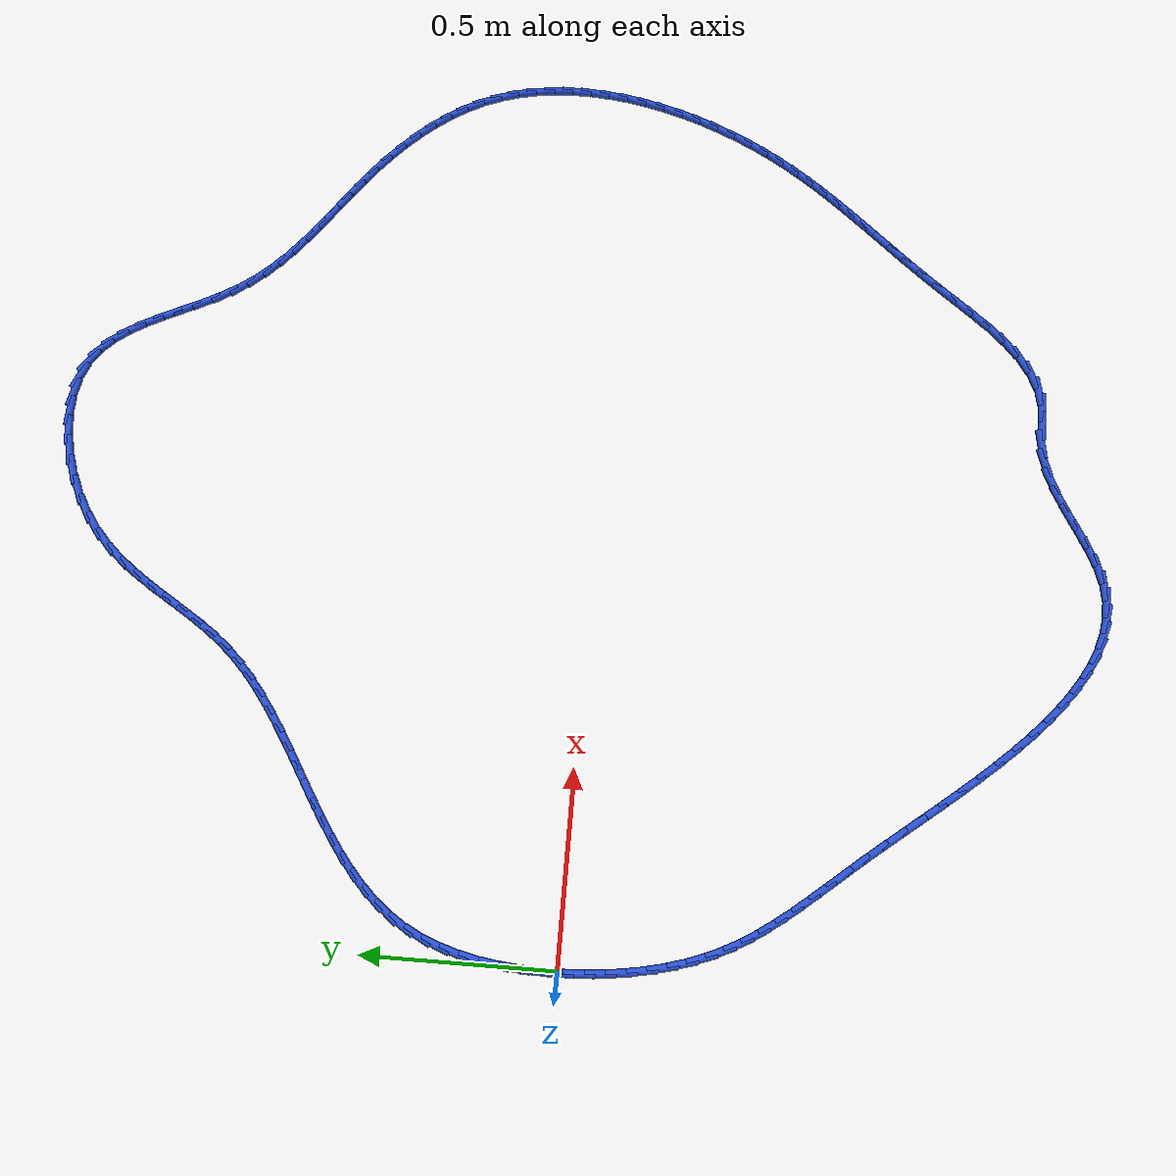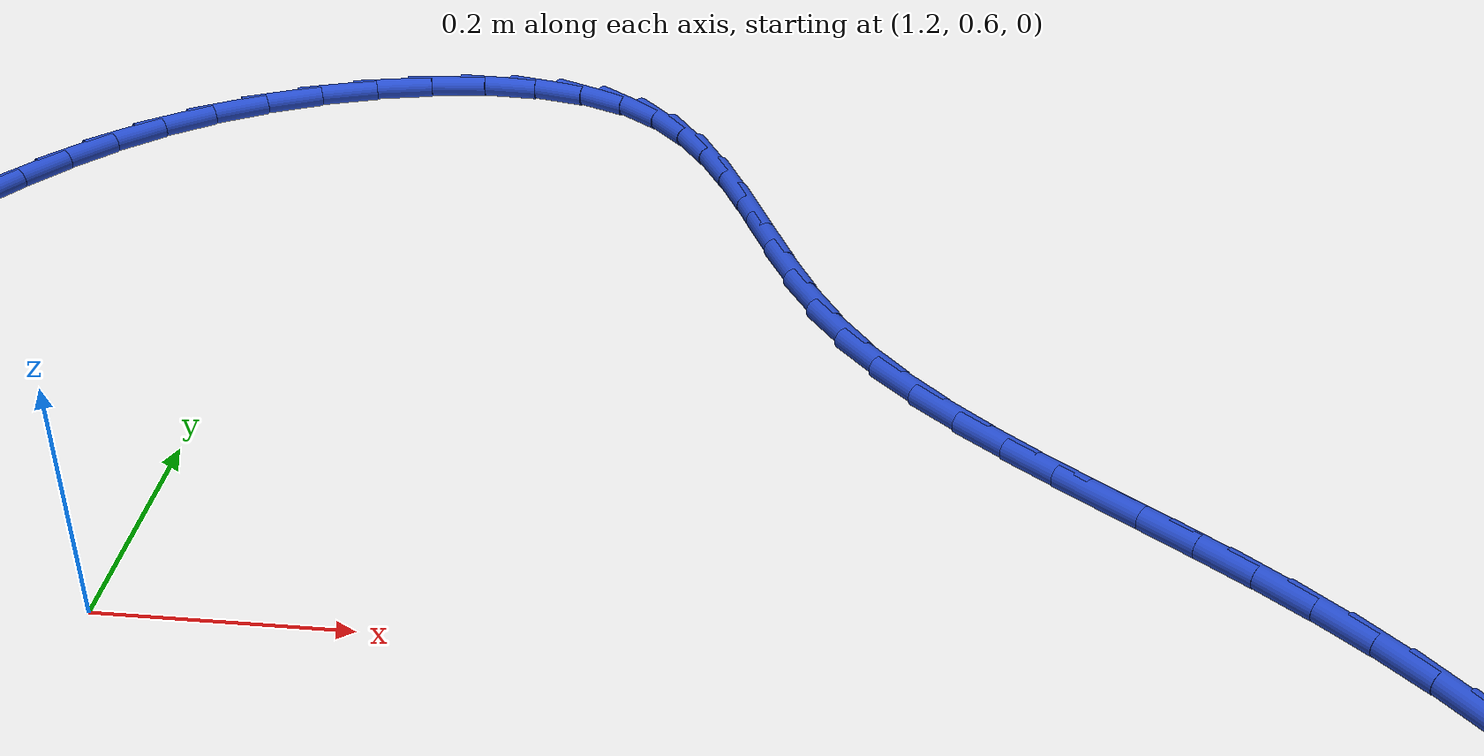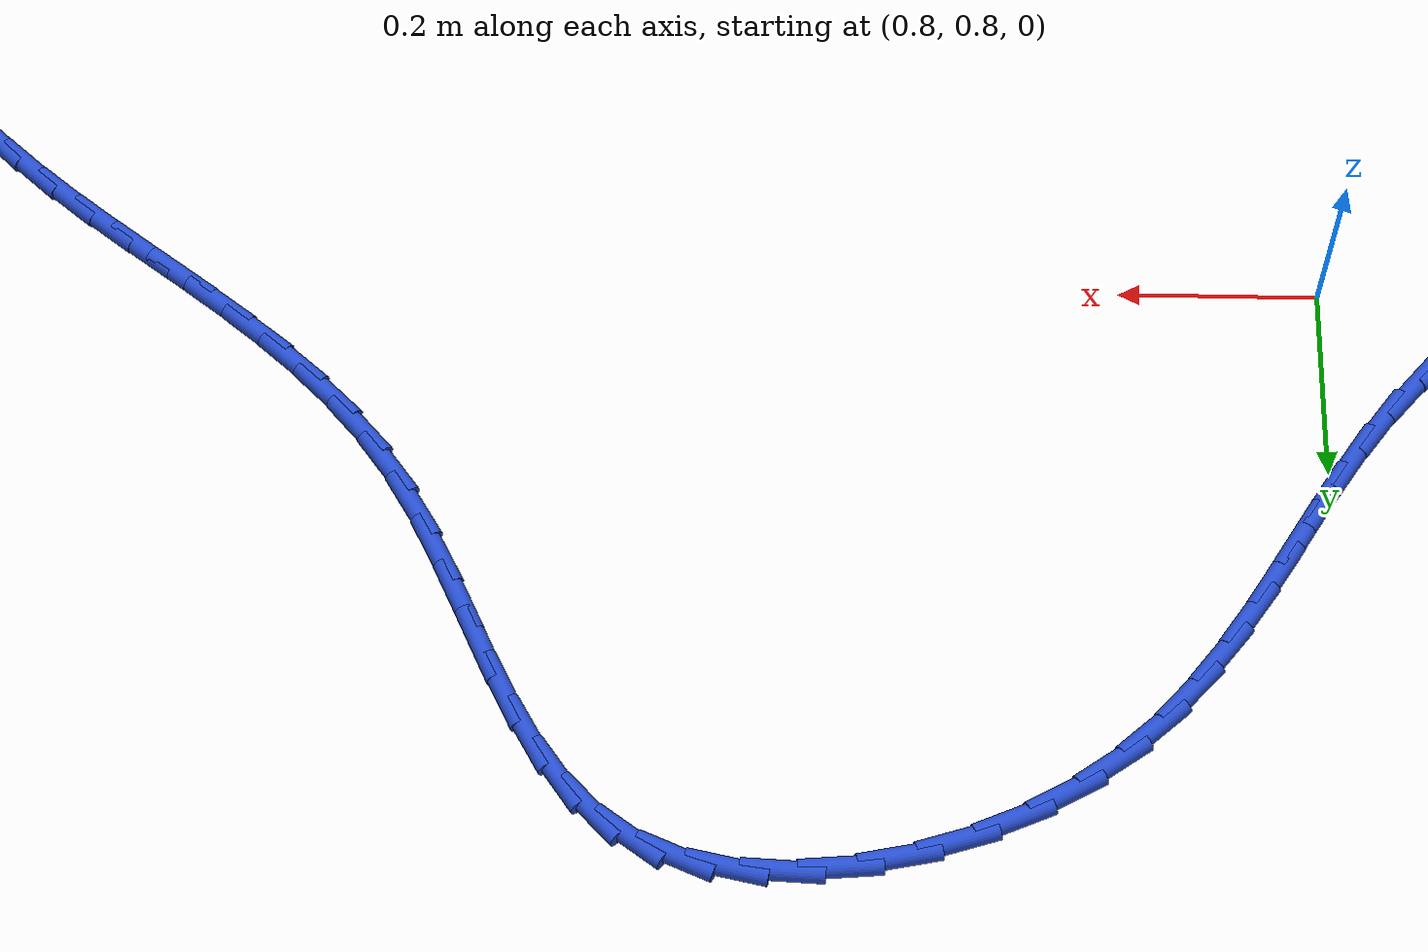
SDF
<sdf version="1.6">
 <world name="default">
  <light name="sun" type="directional">
   <pose>0 0 10 0 -0 0</pose>
   <diffuse>0.8 0.8 0.8 1</diffuse>
   <specular>0.2 0.2 0.2 1</specular>
   <attenuation>
    <range>1000</range>
    <constant>0.9</constant>
    <linear>0.01</linear>
    <quadratic>0.001</quadratic>
   </attenuation>
   <direction>-0.5 0.1 -0.9</direction>
  </light>
  <model name="ground_plane">
   <static>1</static>
   <link name="link">
    <collision name="collision">
     <geometry><plane><normal>0 0 1</normal><size>100 100</size></plane></geometry>
     <surface><friction><ode><mu>100</mu><mu2>50</mu2></ode></friction></surface>
    </collision>
    <visual name="visual">
     <cast_shadows>0</cast_shadows>
     <geometry><plane><normal>0 0 1</normal><size>100 100</size></plane></geometry>
     <material>
      <script><uri>file://media/materials/scripts/gazebo.material</uri><name>Gazebo/WhiteGlow</name></script>
     </material>
    </visual>
   </link>
  </model>
  <gravity>0 0 -9.8</gravity>
  <magnetic_field>6e-06 2.3e-05 -4.2e-05</magnetic_field>
  <atmosphere type="adiabatic"/>
  <physics name="default_physics" default="0" type="ode">
   <max_step_size>0.001</max_step_size>
   <real_time_factor>1</real_time_factor>
   <real_time_update_rate>1000</real_time_update_rate>
  </physics>
  <scene><ambient>0.4 0.4 0.4 1</ambient><background>0.7 0.7 0.7 1</background><shadows>1</shadows></scene>
  <spherical_coordinates>
   <surface_model>EARTH_WGS84</surface_model>
   <latitude_deg>0</latitude_deg>
   <longitude_deg>0</longitude_deg>
   <elevation>0</elevation>
   <heading_deg>0</heading_deg>
  </spherical_coordinates>
  <model name="line">
   <link name="link_0">
    <pose>1.734723475976807e-18 4.163336342344337e-17 0.01 0 1.57 1.5695473844659875</pose>
    <collision name="collision">
     <geometry><cylinder><radius>0.01</radius><length>0.08</length></cylinder></geometry>
    </collision>
    <visual name="visual">
     <material>
      <script><name>Gazebo/Blue</name><uri>file://media/materials/scripts/gazebo.material</uri></script>
     </material>
     <geometry><cylinder><radius>0.01</radius><length>0.08</length></cylinder></geometry>
    </visual>
   </link>
   <link name="link_1">
    <pose>6.664217000441556e-05 0.05335885717946945 0.01 0 1.57 1.5253324503397185</pose>
    <collision name="collision">
     <geometry><cylinder><radius>0.01</radius><length>0.08</length></cylinder></geometry>
    </collision>
    <visual name="visual">
     <material>
      <script><name>Gazebo/Blue</name><uri>file://media/materials/scripts/gazebo.material</uri></script>
     </material>
     <geometry><cylinder><radius>0.01</radius><length>0.08</length></cylinder></geometry>
    </visual>
   </link>
   <link name="link_2">
    <pose>0.0024877650991116233 0.1065759333099808 0.01 0 1.57 1.4750725910085734</pose>
    <collision name="collision">
     <geometry><cylinder><radius>0.01</radius><length>0.08</length></cylinder></geometry>
    </collision>
    <visual name="visual">
     <material>
      <script><name>Gazebo/Blue</name><uri>file://media/materials/scripts/gazebo.material</uri></script>
     </material>
     <geometry><cylinder><radius>0.01</radius><length>0.08</length></cylinder></geometry>
    </visual>
   </link>
   <link name="link_3">
    <pose>0.007543831695108891 0.15923386755550145 0.01 0 1.57 1.4177598399902247</pose>
    <collision name="collision">
     <geometry><cylinder><radius>0.01</radius><length>0.08</length></cylinder></geometry>
    </collision>
    <visual name="visual">
     <material>
      <script><name>Gazebo/Blue</name><uri>file://media/materials/scripts/gazebo.material</uri></script>
     </material>
     <geometry><cylinder><radius>0.01</radius><length>0.08</length></cylinder></geometry>
    </visual>
   </link>
   <link name="link_4">
    <pose>0.01551530486578349 0.2109152990799988 0.01 0 1.57 1.3522727773023824</pose>
    <collision name="collision">
     <geometry><cylinder><radius>0.01</radius><length>0.08</length></cylinder></geometry>
    </collision>
    <visual name="visual">
     <material>
      <script><name>Gazebo/Blue</name><uri>file://media/materials/scripts/gazebo.material</uri></script>
     </material>
     <geometry><cylinder><radius>0.01</radius><length>0.08</length></cylinder></geometry>
    </visual>
   </link>
   <link name="link_5">
    <pose>0.02668264751892268 0.2612028670474401 0.01 0 1.57 1.2774334815352066</pose>
    <collision name="collision">
     <geometry><cylinder><radius>0.01</radius><length>0.08</length></cylinder></geometry>
    </collision>
    <visual name="visual">
     <material>
      <script><name>Gazebo/Blue</name><uri>file://media/materials/scripts/gazebo.material</uri></script>
     </material>
     <geometry><cylinder><radius>0.01</radius><length>0.08</length></cylinder></geometry>
    </visual>
   </link>
   <link name="link_6">
    <pose>0.04132632256231374 0.3096792106217928 0.01 0 1.57 1.1921298426804492</pose>
    <collision name="collision">
     <geometry><cylinder><radius>0.01</radius><length>0.08</length></cylinder></geometry>
    </collision>
    <visual name="visual">
     <material>
      <script><name>Gazebo/Blue</name><uri>file://media/materials/scripts/gazebo.material</uri></script>
     </material>
     <geometry><cylinder><radius>0.01</radius><length>0.08</length></cylinder></geometry>
    </visual>
   </link>
   <link name="link_7">
    <pose>0.059726792903743955 0.35592696896702414 0.01 0 1.57 1.0955327764226392</pose>
    <collision name="collision">
     <geometry><cylinder><radius>0.01</radius><length>0.08</length></cylinder></geometry>
    </collision>
    <visual name="visual">
     <material>
      <script><name>Gazebo/Blue</name><uri>file://media/materials/scripts/gazebo.material</uri></script>
     </material>
     <geometry><cylinder><radius>0.01</radius><length>0.08</length></cylinder></geometry>
    </visual>
   </link>
   <link name="link_8">
    <pose>0.08216452145100056 0.3995287812471016 0.01 0 1.57 0.9894931462684846</pose>
    <collision name="collision">
     <geometry><cylinder><radius>0.01</radius><length>0.08</length></cylinder></geometry>
    </collision>
    <visual name="visual">
     <material>
      <script><name>Gazebo/Blue</name><uri>file://media/materials/scripts/gazebo.material</uri></script>
     </material>
     <geometry><cylinder><radius>0.01</radius><length>0.08</length></cylinder></geometry>
    </visual>
   </link>
   <link name="link_9">
    <pose>0.10884792280902796 0.440140770804454 0.01 0 1.57 0.8891535947270818</pose>
    <collision name="collision">
     <geometry><cylinder><radius>0.01</radius><length>0.08</length></cylinder></geometry>
    </collision>
    <visual name="visual">
     <material>
      <script><name>Gazebo/Blue</name><uri>file://media/materials/scripts/gazebo.material</uri></script>
     </material>
     <geometry><cylinder><radius>0.01</radius><length>0.08</length></cylinder></geometry>
    </visual>
   </link>
   <link name="link_10">
    <pose>0.13949811685095032 0.4779160671790674 0.01 0 1.57 0.8021239914455112</pose>
    <collision name="collision">
     <geometry><cylinder><radius>0.01</radius><length>0.08</length></cylinder></geometry>
    </collision>
    <visual name="visual">
     <material>
      <script><name>Gazebo/Blue</name><uri>file://media/materials/scripts/gazebo.material</uri></script>
     </material>
     <geometry><cylinder><radius>0.01</radius><length>0.08</length></cylinder></geometry>
    </visual>
   </link>
   <link name="link_11">
    <pose>0.1736343247894883 0.5132137222797671 0.01 0 1.57 0.7291288467077437</pose>
    <collision name="collision">
     <geometry><cylinder><radius>0.01</radius><length>0.08</length></cylinder></geometry>
    </collision>
    <visual name="visual">
     <material>
      <script><name>Gazebo/Blue</name><uri>file://media/materials/scripts/gazebo.material</uri></script>
     </material>
     <geometry><cylinder><radius>0.01</radius><length>0.08</length></cylinder></geometry>
    </visual>
   </link>
   <link name="link_12">
    <pose>0.21077512020834177 0.5463934485512226 0.01 0 1.57 0.6699624332969081</pose>
    <collision name="collision">
     <geometry><cylinder><radius>0.01</radius><length>0.08</length></cylinder></geometry>
    </collision>
    <visual name="visual">
     <material>
      <script><name>Gazebo/Blue</name><uri>file://media/materials/scripts/gazebo.material</uri></script>
     </material>
     <geometry><cylinder><radius>0.01</radius><length>0.08</length></cylinder></geometry>
    </visual>
   </link>
   <link name="link_13">
    <pose>0.2504390766912106 0.5778149584381033 0.01 0 1.57 0.6239426441694352</pose>
    <collision name="collision">
     <geometry><cylinder><radius>0.01</radius><length>0.08</length></cylinder></geometry>
    </collision>
    <visual name="visual">
     <material>
      <script><name>Gazebo/Blue</name><uri>file://media/materials/scripts/gazebo.material</uri></script>
     </material>
     <geometry><cylinder><radius>0.01</radius><length>0.08</length></cylinder></geometry>
    </visual>
   </link>
   <link name="link_14">
    <pose>0.29214476782179455 0.6078379643850781 0.01 0 1.57 0.5902428545565552</pose>
    <collision name="collision">
     <geometry><cylinder><radius>0.01</radius><length>0.08</length></cylinder></geometry>
    </collision>
    <visual name="visual">
     <material>
      <script><name>Gazebo/Blue</name><uri>file://media/materials/scripts/gazebo.material</uri></script>
     </material>
     <geometry><cylinder><radius>0.01</radius><length>0.08</length></cylinder></geometry>
    </visual>
   </link>
   <link name="link_15">
    <pose>0.33541076718379365 0.6368221788368166 0.01 0 1.57 0.5681030035859348</pose>
    <collision name="collision">
     <geometry><cylinder><radius>0.01</radius><length>0.08</length></cylinder></geometry>
    </collision>
    <visual name="visual">
     <material>
      <script><name>Gazebo/Blue</name><uri>file://media/materials/scripts/gazebo.material</uri></script>
     </material>
     <geometry><cylinder><radius>0.01</radius><length>0.08</length></cylinder></geometry>
    </visual>
   </link>
   <link name="link_16">
    <pose>0.3797556483609077 0.6651273142379881 0.01 0 1.57 0.5569464916758549</pose>
    <collision name="collision">
     <geometry><cylinder><radius>0.01</radius><length>0.08</length></cylinder></geometry>
    </collision>
    <visual name="visual">
     <material>
      <script><name>Gazebo/Blue</name><uri>file://media/materials/scripts/gazebo.material</uri></script>
     </material>
     <geometry><cylinder><radius>0.01</radius><length>0.08</length></cylinder></geometry>
    </visual>
   </link>
   <link name="link_17">
    <pose>0.4246979849368365 0.6931130830332618 0.01 0 1.57 0.5564360823354563</pose>
    <collision name="collision">
     <geometry><cylinder><radius>0.01</radius><length>0.08</length></cylinder></geometry>
    </collision>
    <visual name="visual">
     <material>
      <script><name>Gazebo/Blue</name><uri>file://media/materials/scripts/gazebo.material</uri></script>
     </material>
     <geometry><cylinder><radius>0.01</radius><length>0.08</length></cylinder></geometry>
    </visual>
   </link>
   <link name="link_18">
    <pose>0.4697563504952801 0.7211391976673073 0.01 0 1.57 0.5664933742057492</pose>
    <collision name="collision">
     <geometry><cylinder><radius>0.01</radius><length>0.08</length></cylinder></geometry>
    </collision>
    <visual name="visual">
     <material>
      <script><name>Gazebo/Blue</name><uri>file://media/materials/scripts/gazebo.material</uri></script>
     </material>
     <geometry><cylinder><radius>0.01</radius><length>0.08</length></cylinder></geometry>
    </visual>
   </link>
   <link name="link_19">
    <pose>0.5144493186199381 0.7495653705847937 0.01 0 1.57 0.5872945978435753</pose>
    <collision name="collision">
     <geometry><cylinder><radius>0.01</radius><length>0.08</length></cylinder></geometry>
    </collision>
    <visual name="visual">
     <material>
      <script><name>Gazebo/Blue</name><uri>file://media/materials/scripts/gazebo.material</uri></script>
     </material>
     <geometry><cylinder><radius>0.01</radius><length>0.08</length></cylinder></geometry>
    </visual>
   </link>
   <link name="link_20">
    <pose>0.5582954628945105 0.7787513142303902 0.01 0 1.57 0.6192442989502459</pose>
    <collision name="collision">
     <geometry><cylinder><radius>0.01</radius><length>0.08</length></cylinder></geometry>
    </collision>
    <visual name="visual">
     <material>
      <script><name>Gazebo/Blue</name><uri>file://media/materials/scripts/gazebo.material</uri></script>
     </material>
     <geometry><cylinder><radius>0.01</radius><length>0.08</length></cylinder></geometry>
    </visual>
   </link>
   <link name="link_21">
    <pose>0.6008133569026974 0.8090567410487669 0.01 0 1.57 0.662918092455319</pose>
    <collision name="collision">
     <geometry><cylinder><radius>0.01</radius><length>0.08</length></cylinder></geometry>
    </collision>
    <visual name="visual">
     <material>
      <script><name>Gazebo/Blue</name><uri>file://media/materials/scripts/gazebo.material</uri></script>
     </material>
     <geometry><cylinder><radius>0.01</radius><length>0.08</length></cylinder></geometry>
    </visual>
   </link>
   <link name="link_22">
    <pose>0.6415215742281982 0.8408413634845918 0.01 0 1.57 0.7189561175364033</pose>
    <collision name="collision">
     <geometry><cylinder><radius>0.01</radius><length>0.08</length></cylinder></geometry>
    </collision>
    <visual name="visual">
     <material>
      <script><name>Gazebo/Blue</name><uri>file://media/materials/scripts/gazebo.material</uri></script>
     </material>
     <geometry><cylinder><radius>0.01</radius><length>0.08</length></cylinder></geometry>
    </visual>
   </link>
   <link name="link_23">
    <pose>0.6799386884547134 0.8744648939825357 0.01 0 1.57 0.787882758871669</pose>
    <collision name="collision">
     <geometry><cylinder><radius>0.01</radius><length>0.08</length></cylinder></geometry>
    </collision>
    <visual name="visual">
     <material>
      <script><name>Gazebo/Blue</name><uri>file://media/materials/scripts/gazebo.material</uri></script>
     </material>
     <geometry><cylinder><radius>0.01</radius><length>0.08</length></cylinder></geometry>
    </visual>
   </link>
   <link name="link_24">
    <pose>0.7155832731659421 0.9102870449872666 0.01 0 1.57 0.8683580052310433</pose>
    <collision name="collision">
     <geometry><cylinder><radius>0.01</radius><length>0.08</length></cylinder></geometry>
    </collision>
    <visual name="visual">
     <material>
      <script><name>Gazebo/Blue</name><uri>file://media/materials/scripts/gazebo.material</uri></script>
     </material>
     <geometry><cylinder><radius>0.01</radius><length>0.08</length></cylinder></geometry>
    </visual>
   </link>
   <link name="link_25">
    <pose>0.74803384354409 0.9486236146467142 0.01 0 1.57 0.9406503862185936</pose>
    <collision name="collision">
     <geometry><cylinder><radius>0.01</radius><length>0.08</length></cylinder></geometry>
    </collision>
    <visual name="visual">
     <material>
      <script><name>Gazebo/Blue</name><uri>file://media/materials/scripts/gazebo.material</uri></script>
     </material>
     <geometry><cylinder><radius>0.01</radius><length>0.08</length></cylinder></geometry>
    </visual>
   </link>
   <link name="link_26">
    <pose>0.7776441356674677 0.9892224602910703 0.01 0 1.57 0.9906803434794265</pose>
    <collision name="collision">
     <geometry><cylinder><radius>0.01</radius><length>0.08</length></cylinder></geometry>
    </collision>
    <visual name="visual">
     <material>
      <script><name>Gazebo/Blue</name><uri>file://media/materials/scripts/gazebo.material</uri></script>
     </material>
     <geometry><cylinder><radius>0.01</radius><length>0.08</length></cylinder></geometry>
    </visual>
   </link>
   <link name="link_27">
    <pose>0.8053079621239113 1.0314357694536997 0.01 0 1.57 1.0182208821904566</pose>
    <collision name="collision">
     <geometry><cylinder><radius>0.01</radius><length>0.08</length></cylinder></geometry>
    </collision>
    <visual name="visual">
     <material>
      <script><name>Gazebo/Blue</name><uri>file://media/materials/scripts/gazebo.material</uri></script>
     </material>
     <geometry><cylinder><radius>0.01</radius><length>0.08</length></cylinder></geometry>
    </visual>
   </link>
   <link name="link_28">
    <pose>0.8319301137915331 1.0746076867744034 0.01 0 1.57 1.0236312018721625</pose>
    <collision name="collision">
     <geometry><cylinder><radius>0.01</radius><length>0.08</length></cylinder></geometry>
    </collision>
    <visual name="visual">
     <material>
      <script><name>Gazebo/Blue</name><uri>file://media/materials/scripts/gazebo.material</uri></script>
     </material>
     <geometry><cylinder><radius>0.01</radius><length>0.08</length></cylinder></geometry>
    </visual>
   </link>
   <link name="link_29">
    <pose>0.8584153815484444 1.1180823568929812 0.01 0 1.57 1.0071734314425185</pose>
    <collision name="collision">
     <geometry><cylinder><radius>0.01</radius><length>0.08</length></cylinder></geometry>
    </collision>
    <visual name="visual">
     <material>
      <script><name>Gazebo/Blue</name><uri>file://media/materials/scripts/gazebo.material</uri></script>
     </material>
     <geometry><cylinder><radius>0.01</radius><length>0.08</length></cylinder></geometry>
    </visual>
   </link>
   <link name="link_30">
    <pose>0.8856685562727566 1.1612039244492327 0.01 0 1.57 0.9689371567399715</pose>
    <collision name="collision">
     <geometry><cylinder><radius>0.01</radius><length>0.08</length></cylinder></geometry>
    </collision>
    <visual name="visual">
     <material>
      <script><name>Gazebo/Blue</name><uri>file://media/materials/scripts/gazebo.material</uri></script>
     </material>
     <geometry><cylinder><radius>0.01</radius><length>0.08</length></cylinder></geometry>
    </visual>
   </link>
   <link name="link_31">
    <pose>0.9145944288425811 1.2033165340829577 0.01 0 1.57 0.9090762703867805</pose>
    <collision name="collision">
     <geometry><cylinder><radius>0.01</radius><length>0.08</length></cylinder></geometry>
    </collision>
    <visual name="visual">
     <material>
      <script><name>Gazebo/Blue</name><uri>file://media/materials/scripts/gazebo.material</uri></script>
     </material>
     <geometry><cylinder><radius>0.01</radius><length>0.08</length></cylinder></geometry>
    </visual>
   </link>
   <link name="link_32">
    <pose>0.9460977901360305 1.2437643304339574 0.01 0 1.57 0.8283394405115861</pose>
    <collision name="collision">
     <geometry><cylinder><radius>0.01</radius><length>0.08</length></cylinder></geometry>
    </collision>
    <visual name="visual">
     <material>
      <script><name>Gazebo/Blue</name><uri>file://media/materials/scripts/gazebo.material</uri></script>
     </material>
     <geometry><cylinder><radius>0.01</radius><length>0.08</length></cylinder></geometry>
    </visual>
   </link>
   <link name="link_33">
    <pose>0.9810834310312156 1.2818914581420313 0.01 0 1.57 0.7288038075218347</pose>
    <collision name="collision">
     <geometry><cylinder><radius>0.01</radius><length>0.08</length></cylinder></geometry>
    </collision>
    <visual name="visual">
     <material>
      <script><name>Gazebo/Blue</name><uri>file://media/materials/scripts/gazebo.material</uri></script>
     </material>
     <geometry><cylinder><radius>0.01</radius><length>0.08</length></cylinder></geometry>
    </visual>
   </link>
   <link name="link_34">
    <pose>1.0204561424062486 1.3170420618469798 0.01 0 1.57 0.6165004382844872</pose>
    <collision name="collision">
     <geometry><cylinder><radius>0.01</radius><length>0.08</length></cylinder></geometry>
    </collision>
    <visual name="visual">
     <material>
      <script><name>Gazebo/Blue</name><uri>file://media/materials/scripts/gazebo.material</uri></script>
     </material>
     <geometry><cylinder><radius>0.01</radius><length>0.08</length></cylinder></geometry>
    </visual>
   </link>
   <link name="link_35">
    <pose>1.0649420999111898 1.3485665454878448 0.01 0 1.57 0.5088439998532955</pose>
    <collision name="collision">
     <geometry><cylinder><radius>0.01</radius><length>0.08</length></cylinder></geometry>
    </collision>
    <visual name="visual">
     <material>
      <script><name>Gazebo/Blue</name><uri>file://media/materials/scripts/gazebo.material</uri></script>
     </material>
     <geometry><cylinder><radius>0.01</radius><length>0.08</length></cylinder></geometry>
    </visual>
   </link>
   <link name="link_36">
    <pose>1.1138762444222594 1.375864066712194 0.01 0 1.57 0.4077946887302013</pose>
    <collision name="collision">
     <geometry><cylinder><radius>0.01</radius><length>0.08</length></cylinder></geometry>
    </collision>
    <visual name="visual">
     <material>
      <script><name>Gazebo/Blue</name><uri>file://media/materials/scripts/gazebo.material</uri></script>
     </material>
     <geometry><cylinder><radius>0.01</radius><length>0.08</length></cylinder></geometry>
    </visual>
   </link>
   <link name="link_37">
    <pose>1.165940986674657 1.3983566500947984 0.01 0 1.57 0.3075145787612556</pose>
    <collision name="collision">
     <geometry><cylinder><radius>0.01</radius><length>0.08</length></cylinder></geometry>
    </collision>
    <visual name="visual">
     <material>
      <script><name>Gazebo/Blue</name><uri>file://media/materials/scripts/gazebo.material</uri></script>
     </material>
     <geometry><cylinder><radius>0.01</radius><length>0.08</length></cylinder></geometry>
    </visual>
   </link>
   <link name="link_38">
    <pose>1.2198149849205389 1.4154664517104956 0.01 0 1.57 0.20228657717183465</pose>
    <collision name="collision">
     <geometry><cylinder><radius>0.01</radius><length>0.08</length></cylinder></geometry>
    </collision>
    <visual name="visual">
     <material>
      <script><name>Gazebo/Blue</name><uri>file://media/materials/scripts/gazebo.material</uri></script>
     </material>
     <geometry><cylinder><radius>0.01</radius><length>0.08</length></cylinder></geometry>
    </visual>
   </link>
   <link name="link_39">
    <pose>1.2741768974120609 1.426615627634123 0.01 0 1.57 0.08592348556246679</pose>
    <collision name="collision">
     <geometry><cylinder><radius>0.01</radius><length>0.08</length></cylinder></geometry>
    </collision>
    <visual name="visual">
     <material>
      <script><name>Gazebo/Blue</name><uri>file://media/materials/scripts/gazebo.material</uri></script>
     </material>
     <geometry><cylinder><radius>0.01</radius><length>0.08</length></cylinder></geometry>
    </visual>
   </link>
   <link name="link_40">
    <pose>1.3277053824013783 1.4312263339405178 0.01 0 1.57 -0.04873354622593823</pose>
    <collision name="collision">
     <geometry><cylinder><radius>0.01</radius><length>0.08</length></cylinder></geometry>
    </collision>
    <visual name="visual">
     <material>
      <script><name>Gazebo/Blue</name><uri>file://media/materials/scripts/gazebo.material</uri></script>
     </material>
     <geometry><cylinder><radius>0.01</radius><length>0.08</length></cylinder></geometry>
    </visual>
   </link>
   <link name="link_41">
    <pose>1.379079098140648 1.428720726704518 0.01 0 1.57 -0.20981530748769567</pose>
    <collision name="collision">
     <geometry><cylinder><radius>0.01</radius><length>0.08</length></cylinder></geometry>
    </collision>
    <visual name="visual">
     <material>
      <script><name>Gazebo/Blue</name><uri>file://media/materials/scripts/gazebo.material</uri></script>
     </material>
     <geometry><cylinder><radius>0.01</radius><length>0.08</length></cylinder></geometry>
    </visual>
   </link>
   <link name="link_42">
    <pose>1.4269767028820246 1.418520962000961 0.01 0 1.57 -0.40489712538913775</pose>
    <collision name="collision">
     <geometry><cylinder><radius>0.01</radius><length>0.08</length></cylinder></geometry>
    </collision>
    <visual name="visual">
     <material>
      <script><name>Gazebo/Blue</name><uri>file://media/materials/scripts/gazebo.material</uri></script>
     </material>
     <geometry><cylinder><radius>0.01</radius><length>0.08</length></cylinder></geometry>
    </visual>
   </link>
   <link name="link_43">
    <pose>1.4700768548782919 1.4000491959052153 0.01 0 1.57 -0.6251507552929085</pose>
    <collision name="collision">
     <geometry><cylinder><radius>0.01</radius><length>0.08</length></cylinder></geometry>
    </collision>
    <visual name="visual">
     <material>
      <script><name>Gazebo/Blue</name><uri>file://media/materials/scripts/gazebo.material</uri></script>
     </material>
     <geometry><cylinder><radius>0.01</radius><length>0.08</length></cylinder></geometry>
    </visual>
   </link>
   <link name="link_44">
    <pose>1.507461090694306 1.3730684809265739 0.01 0 1.57 -0.8155432820982105</pose>
    <collision name="collision">
     <geometry><cylinder><radius>0.01</radius><length>0.08</length></cylinder></geometry>
    </collision>
    <visual name="visual">
     <material>
      <script><name>Gazebo/Blue</name><uri>file://media/materials/scripts/gazebo.material</uri></script>
     </material>
     <geometry><cylinder><radius>0.01</radius><length>0.08</length></cylinder></geometry>
    </visual>
   </link>
   <link name="link_45">
    <pose>1.5398168581401075 1.338700715161892 0.01 0 1.57 -0.9566017665198467</pose>
    <collision name="collision">
     <geometry><cylinder><radius>0.01</radius><length>0.08</length></cylinder></geometry>
    </collision>
    <visual name="visual">
     <material>
      <script><name>Gazebo/Blue</name><uri>file://media/materials/scripts/gazebo.material</uri></script>
     </material>
     <geometry><cylinder><radius>0.01</radius><length>0.08</length></cylinder></geometry>
    </visual>
   </link>
   <link name="link_46">
    <pose>1.5682316872013022 1.298406327184449 0.01 0 1.57 -1.0519206408664372</pose>
    <collision name="collision">
     <geometry><cylinder><radius>0.01</radius><length>0.08</length></cylinder></geometry>
    </collision>
    <visual name="visual">
     <material>
      <script><name>Gazebo/Blue</name><uri>file://media/materials/scripts/gazebo.material</uri></script>
     </material>
     <geometry><cylinder><radius>0.01</radius><length>0.08</length></cylinder></geometry>
    </visual>
   </link>
   <link name="link_47">
    <pose>1.5937931078634957 1.2536457455675247 0.01 0 1.57 -1.1086174570124634</pose>
    <collision name="collision">
     <geometry><cylinder><radius>0.01</radius><length>0.08</length></cylinder></geometry>
    </collision>
    <visual name="visual">
     <material>
      <script><name>Gazebo/Blue</name><uri>file://media/materials/scripts/gazebo.material</uri></script>
     </material>
     <geometry><cylinder><radius>0.01</radius><length>0.08</length></cylinder></geometry>
    </visual>
   </link>
   <link name="link_48">
    <pose>1.6175886501122934 1.2058793988843974 0.01 0 1.57 -1.1324208240397309</pose>
    <collision name="collision">
     <geometry><cylinder><radius>0.01</radius><length>0.08</length></cylinder></geometry>
    </collision>
    <visual name="visual">
     <material>
      <script><name>Gazebo/Blue</name><uri>file://media/materials/scripts/gazebo.material</uri></script>
     </material>
     <geometry><cylinder><radius>0.01</radius><length>0.08</length></cylinder></geometry>
    </visual>
   </link>
   <link name="link_49">
    <pose>1.6407058439333004 1.156567715708347 0.01 0 1.57 -1.1263079886998069</pose>
    <collision name="collision">
     <geometry><cylinder><radius>0.01</radius><length>0.08</length></cylinder></geometry>
    </collision>
    <visual name="visual">
     <material>
      <script><name>Gazebo/Blue</name><uri>file://media/materials/scripts/gazebo.material</uri></script>
     </material>
     <geometry><cylinder><radius>0.01</radius><length>0.08</length></cylinder></geometry>
    </visual>
   </link>
   <link name="link_50">
    <pose>1.6642322193121228 1.1071711246126517 0.01 0 1.57 -1.0904229031835548</pose>
    <collision name="collision">
     <geometry><cylinder><radius>0.01</radius><length>0.08</length></cylinder></geometry>
    </collision>
    <visual name="visual">
     <material>
      <script><name>Gazebo/Blue</name><uri>file://media/materials/scripts/gazebo.material</uri></script>
     </material>
     <geometry><cylinder><radius>0.01</radius><length>0.08</length></cylinder></geometry>
    </visual>
   </link>
   <link name="link_51">
    <pose>1.6892553062343658 1.0591500541705918 0.01 0 1.57 -1.0223806855809172</pose>
    <collision name="collision">
     <geometry><cylinder><radius>0.01</radius><length>0.08</length></cylinder></geometry>
    </collision>
    <visual name="visual">
     <material>
      <script><name>Gazebo/Blue</name><uri>file://media/materials/scripts/gazebo.material</uri></script>
     </material>
     <geometry><cylinder><radius>0.01</radius><length>0.08</length></cylinder></geometry>
    </visual>
   </link>
   <link name="link_52">
    <pose>1.7168612485237094 1.0139631108461111 0.01 0 1.57 -0.930736231398435</pose>
    <collision name="collision">
     <geometry><cylinder><radius>0.01</radius><length>0.08</length></cylinder></geometry>
    </collision>
    <visual name="visual">
     <material>
      <script><name>Gazebo/Blue</name><uri>file://media/materials/scripts/gazebo.material</uri></script>
     </material>
     <geometry><cylinder><radius>0.01</radius><length>0.08</length></cylinder></geometry>
    </visual>
   </link>
   <link name="link_53">
    <pose>1.7477199884503813 0.9725218043155802 0.01 0 1.57 -0.8453038112708021</pose>
    <collision name="collision">
     <geometry><cylinder><radius>0.01</radius><length>0.08</length></cylinder></geometry>
    </collision>
    <visual name="visual">
     <material>
      <script><name>Gazebo/Blue</name><uri>file://media/materials/scripts/gazebo.material</uri></script>
     </material>
     <geometry><cylinder><radius>0.01</radius><length>0.08</length></cylinder></geometry>
    </visual>
   </link>
   <link name="link_54">
    <pose>1.7815040798169304 0.9344265774847251 0.01 0 1.57 -0.772899238820326</pose>
    <collision name="collision">
     <geometry><cylinder><radius>0.01</radius><length>0.08</length></cylinder></geometry>
    </collision>
    <visual name="visual">
     <material>
      <script><name>Gazebo/Blue</name><uri>file://media/materials/scripts/gazebo.material</uri></script>
     </material>
     <geometry><cylinder><radius>0.01</radius><length>0.08</length></cylinder></geometry>
    </visual>
   </link>
   <link name="link_55">
    <pose>1.8177397753169198 0.8990855605057954 0.01 0 1.57 -0.714990599709199</pose>
    <collision name="collision">
     <geometry><cylinder><radius>0.01</radius><length>0.08</length></cylinder></geometry>
    </collision>
    <visual name="visual">
     <material>
      <script><name>Gazebo/Blue</name><uri>file://media/materials/scripts/gazebo.material</uri></script>
     </material>
     <geometry><cylinder><radius>0.01</radius><length>0.08</length></cylinder></geometry>
    </visual>
   </link>
   <link name="link_56">
    <pose>1.8559533276439113 0.8659068835310403 0.01 0 1.57 -0.6721884574658633</pose>
    <collision name="collision">
     <geometry><cylinder><radius>0.01</radius><length>0.08</length></cylinder></geometry>
    </collision>
    <visual name="visual">
     <material>
      <script><name>Gazebo/Blue</name><uri>file://media/materials/scripts/gazebo.material</uri></script>
     </material>
     <geometry><cylinder><radius>0.01</radius><length>0.08</length></cylinder></geometry>
    </visual>
   </link>
   <link name="link_57">
    <pose>1.8956709894914667 0.834298676712709 0.01 0 1.57 -0.6445775085181882</pose>
    <collision name="collision">
     <geometry><cylinder><radius>0.01</radius><length>0.08</length></cylinder></geometry>
    </collision>
    <visual name="visual">
     <material>
      <script><name>Gazebo/Blue</name><uri>file://media/materials/scripts/gazebo.material</uri></script>
     </material>
     <geometry><cylinder><radius>0.01</radius><length>0.08</length></cylinder></geometry>
    </visual>
   </link>
   <link name="link_58">
    <pose>1.9364190135531498 0.8036690702030509 0.01 0 1.57 -0.6320054437416739</pose>
    <collision name="collision">
     <geometry><cylinder><radius>0.01</radius><length>0.08</length></cylinder></geometry>
    </collision>
    <visual name="visual">
     <material>
      <script><name>Gazebo/Blue</name><uri>file://media/materials/scripts/gazebo.material</uri></script>
     </material>
     <geometry><cylinder><radius>0.01</radius><length>0.08</length></cylinder></geometry>
    </visual>
   </link>
   <link name="link_59">
    <pose>1.9777236525225201 0.7734261941543157 0.01 0 1.57 -0.6342739955631425</pose>
    <collision name="collision">
     <geometry><cylinder><radius>0.01</radius><length>0.08</length></cylinder></geometry>
    </collision>
    <visual name="visual">
     <material>
      <script><name>Gazebo/Blue</name><uri>file://media/materials/scripts/gazebo.material</uri></script>
     </material>
     <geometry><cylinder><radius>0.01</radius><length>0.08</length></cylinder></geometry>
    </visual>
   </link>
   <link name="link_60">
    <pose>2.019111159093141 0.7429781787187526 0.01 0 1.57 -0.6512233123907576</pose>
    <collision name="collision">
     <geometry><cylinder><radius>0.01</radius><length>0.08</length></cylinder></geometry>
    </collision>
    <visual name="visual">
     <material>
      <script><name>Gazebo/Blue</name><uri>file://media/materials/scripts/gazebo.material</uri></script>
     </material>
     <geometry><cylinder><radius>0.01</radius><length>0.08</length></cylinder></geometry>
    </visual>
   </link>
   <link name="link_61">
    <pose>2.060107785958576 0.7117331540486113 0.01 0 1.57 -0.6827106466123564</pose>
    <collision name="collision">
     <geometry><cylinder><radius>0.01</radius><length>0.08</length></cylinder></geometry>
    </collision>
    <visual name="visual">
     <material>
      <script><name>Gazebo/Blue</name><uri>file://media/materials/scripts/gazebo.material</uri></script>
     </material>
     <geometry><cylinder><radius>0.01</radius><length>0.08</length></cylinder></geometry>
    </visual>
   </link>
   <link name="link_62">
    <pose>2.100239814370191 0.6790996160182421 0.01 0 1.57 -0.7261479364947004</pose>
    <collision name="collision">
     <geometry><cylinder><radius>0.01</radius><length>0.08</length></cylinder></geometry>
    </collision>
    <visual name="visual">
     <material>
      <script><name>Gazebo/Blue</name><uri>file://media/materials/scripts/gazebo.material</uri></script>
     </material>
     <geometry><cylinder><radius>0.01</radius><length>0.08</length></cylinder></geometry>
    </visual>
   </link>
   <link name="link_63">
    <pose>2.1390455433337525 0.6446399644314451 0.01 0 1.57 -0.7756309951111536</pose>
    <collision name="collision">
     <geometry><cylinder><radius>0.01</radius><length>0.08</length></cylinder></geometry>
    </collision>
    <visual name="visual">
     <material>
      <script><name>Gazebo/Blue</name><uri>file://media/materials/scripts/gazebo.material</uri></script>
     </material>
     <geometry><cylinder><radius>0.01</radius><length>0.08</length></cylinder></geometry>
    </visual>
   </link>
   <link name="link_64">
    <pose>2.176093864486659 0.6083083799574216 0.01 0 1.57 -0.830858863072188</pose>
    <collision name="collision">
     <geometry><cylinder><radius>0.01</radius><length>0.08</length></cylinder></geometry>
    </collision>
    <visual name="visual">
     <material>
      <script><name>Gazebo/Blue</name><uri>file://media/materials/scripts/gazebo.material</uri></script>
     </material>
     <geometry><cylinder><radius>0.01</radius><length>0.08</length></cylinder></geometry>
    </visual>
   </link>
   <link name="link_65">
    <pose>2.21095846606959 0.5701204703896781 0.01 0 1.57 -0.8925363238286338</pose>
    <collision name="collision">
     <geometry><cylinder><radius>0.01</radius><length>0.08</length></cylinder></geometry>
    </collision>
    <visual name="visual">
     <material>
      <script><name>Gazebo/Blue</name><uri>file://media/materials/scripts/gazebo.material</uri></script>
     </material>
     <geometry><cylinder><radius>0.01</radius><length>0.08</length></cylinder></geometry>
    </visual>
   </link>
   <link name="link_66">
    <pose>2.243213036323226 0.5300918435217211 0.01 0 1.57 -0.9613445193581414</pose>
    <collision name="collision">
     <geometry><cylinder><radius>0.01</radius><length>0.08</length></cylinder></geometry>
    </collision>
    <visual name="visual">
     <material>
      <script><name>Gazebo/Blue</name><uri>file://media/materials/scripts/gazebo.material</uri></script>
     </material>
     <geometry><cylinder><radius>0.01</radius><length>0.08</length></cylinder></geometry>
    </visual>
   </link>
   <link name="link_67">
    <pose>2.2724312634882455 0.4882381071470561 0.01 0 1.57 -1.0378597064188972</pose>
    <collision name="collision">
     <geometry><cylinder><radius>0.01</radius><length>0.08</length></cylinder></geometry>
    </collision>
    <visual name="visual">
     <material>
      <script><name>Gazebo/Blue</name><uri>file://media/materials/scripts/gazebo.material</uri></script>
     </material>
     <geometry><cylinder><radius>0.01</radius><length>0.08</length></cylinder></geometry>
    </visual>
   </link>
   <link name="link_68">
    <pose>2.298186835805331 0.44457486905919097 0.01 0 1.57 -1.1224304173334703</pose>
    <collision name="collision">
     <geometry><cylinder><radius>0.01</radius><length>0.08</length></cylinder></geometry>
    </collision>
    <visual name="visual">
     <material>
      <script><name>Gazebo/Blue</name><uri>file://media/materials/scripts/gazebo.material</uri></script>
     </material>
     <geometry><cylinder><radius>0.01</radius><length>0.08</length></cylinder></geometry>
    </visual>
   </link>
   <link name="link_69">
    <pose>2.3200535700337492 0.3991177824876608 0.01 0 1.57 -1.2121285092722933</pose>
    <collision name="collision">
     <geometry><cylinder><radius>0.01</radius><length>0.08</length></cylinder></geometry>
    </collision>
    <visual name="visual">
     <material>
      <script><name>Gazebo/Blue</name><uri>file://media/materials/scripts/gazebo.material</uri></script>
     </material>
     <geometry><cylinder><radius>0.01</radius><length>0.08</length></cylinder></geometry>
    </visual>
   </link>
   <link name="link_70">
    <pose>2.3377430063213276 0.351931190925309 0.01 0 1.57 -1.2980858838007057</pose>
    <collision name="collision">
     <geometry><cylinder><radius>0.01</radius><length>0.08</length></cylinder></geometry>
    </collision>
    <visual name="visual">
     <material>
      <script><name>Gazebo/Blue</name><uri>file://media/materials/scripts/gazebo.material</uri></script>
     </material>
     <geometry><cylinder><radius>0.01</radius><length>0.08</length></cylinder></geometry>
    </visual>
   </link>
   <link name="link_71">
    <pose>2.3513662754836653 0.30322070780491533 0.01 0 1.57 -1.3784124267918456</pose>
    <collision name="collision">
     <geometry><cylinder><radius>0.01</radius><length>0.08</length></cylinder></geometry>
    </collision>
    <visual name="visual">
     <material>
      <script><name>Gazebo/Blue</name><uri>file://media/materials/scripts/gazebo.material</uri></script>
     </material>
     <geometry><cylinder><radius>0.01</radius><length>0.08</length></cylinder></geometry>
    </visual>
   </link>
   <link name="link_72">
    <pose>2.361106567945751 0.25321742227106026 0.01 0 1.57 -1.4530529351187311</pose>
    <collision name="collision">
     <geometry><cylinder><radius>0.01</radius><length>0.08</length></cylinder></geometry>
    </collision>
    <visual name="visual">
     <material>
      <script><name>Gazebo/Blue</name><uri>file://media/materials/scripts/gazebo.material</uri></script>
     </material>
     <geometry><cylinder><radius>0.01</radius><length>0.08</length></cylinder></geometry>
    </visual>
   </link>
   <link name="link_73">
    <pose>2.3671470741325717 0.2021524234683227 0.01 0 1.57 -1.5222002588055192</pose>
    <collision name="collision">
     <geometry><cylinder><radius>0.01</radius><length>0.08</length></cylinder></geometry>
    </collision>
    <visual name="visual">
     <material>
      <script><name>Gazebo/Blue</name><uri>file://media/materials/scripts/gazebo.material</uri></script>
     </material>
     <geometry><cylinder><radius>0.01</radius><length>0.08</length></cylinder></geometry>
    </visual>
   </link>
   <link name="link_74">
    <pose>2.3696709844691153 0.15025680054128246 0.01 0 1.57 1.5553771725827126</pose>
    <collision name="collision">
     <geometry><cylinder><radius>0.01</radius><length>0.08</length></cylinder></geometry>
    </collision>
    <visual name="visual">
     <material>
      <script><name>Gazebo/Blue</name><uri>file://media/materials/scripts/gazebo.material</uri></script>
     </material>
     <geometry><cylinder><radius>0.01</radius><length>0.08</length></cylinder></geometry>
    </visual>
   </link>
   <link name="link_75">
    <pose>2.36886148938037 0.09776164263451902 0.01 0 1.57 1.4960316659950188</pose>
    <collision name="collision">
     <geometry><cylinder><radius>0.01</radius><length>0.08</length></cylinder></geometry>
    </collision>
    <visual name="visual">
     <material>
      <script><name>Gazebo/Blue</name><uri>file://media/materials/scripts/gazebo.material</uri></script>
     </material>
     <geometry><cylinder><radius>0.01</radius><length>0.08</length></cylinder></geometry>
    </visual>
   </link>
   <link name="link_76">
    <pose>2.3649017792913236 0.04489803889261144 0.01 0 1.57 1.4408421237259572</pose>
    <collision name="collision">
     <geometry><cylinder><radius>0.01</radius><length>0.08</length></cylinder></geometry>
    </collision>
    <visual name="visual">
     <material>
      <script><name>Gazebo/Blue</name><uri>file://media/materials/scripts/gazebo.material</uri></script>
     </material>
     <geometry><cylinder><radius>0.01</radius><length>0.08</length></cylinder></geometry>
    </visual>
   </link>
   <link name="link_77">
    <pose>2.3579750446269636 -0.00810292153986026 0.01 0 1.57 1.3892770488132746</pose>
    <collision name="collision">
     <geometry><cylinder><radius>0.01</radius><length>0.08</length></cylinder></geometry>
    </collision>
    <visual name="visual">
     <material>
      <script><name>Gazebo/Blue</name><uri>file://media/materials/scripts/gazebo.material</uri></script>
     </material>
     <geometry><cylinder><radius>0.01</radius><length>0.08</length></cylinder></geometry>
    </visual>
   </link>
   <link name="link_78">
    <pose>2.3482644758122775 -0.06101014951831565 0.01 0 1.57 1.3408073047150721</pose>
    <collision name="collision">
     <geometry><cylinder><radius>0.01</radius><length>0.08</length></cylinder></geometry>
    </collision>
    <visual name="visual">
     <material>
      <script><name>Gazebo/Blue</name><uri>file://media/materials/scripts/gazebo.material</uri></script>
     </material>
     <geometry><cylinder><radius>0.01</radius><length>0.08</length></cylinder></geometry>
    </visual>
   </link>
   <link name="link_79">
    <pose>2.335953263272254 -0.11359255589817692 0.01 0 1.57 1.2949159385856528</pose>
    <collision name="collision">
     <geometry><cylinder><radius>0.01</radius><length>0.08</length></cylinder></geometry>
    </collision>
    <visual name="visual">
     <material>
      <script><name>Gazebo/Blue</name><uri>file://media/materials/scripts/gazebo.material</uri></script>
     </material>
     <geometry><cylinder><radius>0.01</radius><length>0.08</length></cylinder></geometry>
    </visual>
   </link>
   <link name="link_80">
    <pose>2.32122459743188 -0.16561905153486278 0.01 0 1.57 1.2511005310031922</pose>
    <collision name="collision">
     <geometry><cylinder><radius>0.01</radius><length>0.08</length></cylinder></geometry>
    </collision>
    <visual name="visual">
     <material>
      <script><name>Gazebo/Blue</name><uri>file://media/materials/scripts/gazebo.material</uri></script>
     </material>
     <geometry><cylinder><radius>0.01</radius><length>0.08</length></cylinder></geometry>
    </visual>
   </link>
   <link name="link_81">
    <pose>2.304261668716143 -0.21685854728379544 0.01 0 1.57 1.2088701583974053</pose>
    <collision name="collision">
     <geometry><cylinder><radius>0.01</radius><length>0.08</length></cylinder></geometry>
    </collision>
    <visual name="visual">
     <material>
      <script><name>Gazebo/Blue</name><uri>file://media/materials/scripts/gazebo.material</uri></script>
     </material>
     <geometry><cylinder><radius>0.01</radius><length>0.08</length></cylinder></geometry>
    </visual>
   </link>
   <link name="link_82">
    <pose>2.2852476675500313 -0.2670799540003944 0.01 0 1.57 1.1677383058425364</pose>
    <collision name="collision">
     <geometry><cylinder><radius>0.01</radius><length>0.08</length></cylinder></geometry>
    </collision>
    <visual name="visual">
     <material>
      <script><name>Gazebo/Blue</name><uri>file://media/materials/scripts/gazebo.material</uri></script>
     </material>
     <geometry><cylinder><radius>0.01</radius><length>0.08</length></cylinder></geometry>
    </visual>
   </link>
   <link name="link_83">
    <pose>2.2643657843585325 -0.3160521825400793 0.01 0 1.57 1.1272123939795518</pose>
    <collision name="collision">
     <geometry><cylinder><radius>0.01</radius><length>0.08</length></cylinder></geometry>
    </collision>
    <visual name="visual">
     <material>
      <script><name>Gazebo/Blue</name><uri>file://media/materials/scripts/gazebo.material</uri></script>
     </material>
     <geometry><cylinder><radius>0.01</radius><length>0.08</length></cylinder></geometry>
    </visual>
   </link>
   <link name="link_84">
    <pose>2.2417992095666346 -0.36354414375827226 0.01 0 1.57 1.0867799917671845</pose>
    <collision name="collision">
     <geometry><cylinder><radius>0.01</radius><length>0.08</length></cylinder></geometry>
    </collision>
    <visual name="visual">
     <material>
      <script><name>Gazebo/Blue</name><uri>file://media/materials/scripts/gazebo.material</uri></script>
     </material>
     <geometry><cylinder><radius>0.01</radius><length>0.08</length></cylinder></geometry>
    </visual>
   </link>
   <link name="link_85">
    <pose>2.217731133568367 -0.40932474873902086 0.01 0 1.57 1.0466288748015282</pose>
    <collision name="collision">
     <geometry><cylinder><radius>0.01</radius><length>0.08</length></cylinder></geometry>
    </collision>
    <visual name="visual">
     <material>
      <script><name>Gazebo/Blue</name><uri>file://media/materials/scripts/gazebo.material</uri></script>
     </material>
     <geometry><cylinder><radius>0.01</radius><length>0.08</length></cylinder></geometry>
    </visual>
   </link>
   <link name="link_86">
    <pose>2.1923315444752087 -0.45326040779905746 0.01 0 1.57 1.0095762652193239</pose>
    <collision name="collision">
     <geometry><cylinder><radius>0.01</radius><length>0.08</length></cylinder></geometry>
    </collision>
    <visual name="visual">
     <material>
      <script><name>Gazebo/Blue</name><uri>file://media/materials/scripts/gazebo.material</uri></script>
     </material>
     <geometry><cylinder><radius>0.01</radius><length>0.08</length></cylinder></geometry>
    </visual>
   </link>
   <link name="link_87">
    <pose>2.1657197114305498 -0.49559209227912004 0.01 0 1.57 0.9770061520092153</pose>
    <collision name="collision">
     <geometry><cylinder><radius>0.01</radius><length>0.08</length></cylinder></geometry>
    </collision>
    <visual name="visual">
     <material>
      <script><name>Gazebo/Blue</name><uri>file://media/materials/scripts/gazebo.material</uri></script>
     </material>
     <geometry><cylinder><radius>0.01</radius><length>0.08</length></cylinder></geometry>
    </visual>
   </link>
   <link name="link_88">
    <pose>2.138002725852883 -0.5366507063651704 0.01 0 1.57 0.9495499112246137</pose>
    <collision name="collision">
     <geometry><cylinder><radius>0.01</radius><length>0.08</length></cylinder></geometry>
    </collision>
    <visual name="visual">
     <material>
      <script><name>Gazebo/Blue</name><uri>file://media/materials/scripts/gazebo.material</uri></script>
     </material>
     <geometry><cylinder><radius>0.01</radius><length>0.08</length></cylinder></geometry>
    </visual>
   </link>
   <link name="link_89">
    <pose>2.109287679160701 -0.5767671542431724 0.01 0 1.57 0.9276658729128038</pose>
    <collision name="collision">
     <geometry><cylinder><radius>0.01</radius><length>0.08</length></cylinder></geometry>
    </collision>
    <visual name="visual">
     <material>
      <script><name>Gazebo/Blue</name><uri>file://media/materials/scripts/gazebo.material</uri></script>
     </material>
     <geometry><cylinder><radius>0.01</radius><length>0.08</length></cylinder></geometry>
    </visual>
   </link>
   <link name="link_90">
    <pose>2.0796816627724986 -0.6162723400990876 0.01 0 1.57 0.9116351513699099</pose>
    <collision name="collision">
     <geometry><cylinder><radius>0.01</radius><length>0.08</length></cylinder></geometry>
    </collision>
    <visual name="visual">
     <material>
      <script><name>Gazebo/Blue</name><uri>file://media/materials/scripts/gazebo.material</uri></script>
     </material>
     <geometry><cylinder><radius>0.01</radius><length>0.08</length></cylinder></geometry>
    </visual>
   </link>
   <link name="link_91">
    <pose>2.0492917681067695 -0.6554971681188778 0.01 0 1.57 0.9015695190994819</pose>
    <collision name="collision">
     <geometry><cylinder><radius>0.01</radius><length>0.08</length></cylinder></geometry>
    </collision>
    <visual name="visual">
     <material>
      <script><name>Gazebo/Blue</name><uri>file://media/materials/scripts/gazebo.material</uri></script>
     </material>
     <geometry><cylinder><radius>0.01</radius><length>0.08</length></cylinder></geometry>
    </visual>
   </link>
   <link name="link_92">
    <pose>2.0182250865820053 -0.6947725424885067 0.01 0 1.57 0.8974266095816686</pose>
    <collision name="collision">
     <geometry><cylinder><radius>0.01</radius><length>0.08</length></cylinder></geometry>
    </collision>
    <visual name="visual">
     <material>
      <script><name>Gazebo/Blue</name><uri>file://media/materials/scripts/gazebo.material</uri></script>
     </material>
     <geometry><cylinder><radius>0.01</radius><length>0.08</length></cylinder></geometry>
    </visual>
   </link>
   <link name="link_93">
    <pose>1.9865887096167005 -0.7344293673939353 0.01 0 1.57 0.8990283898471098</pose>
    <collision name="collision">
     <geometry><cylinder><radius>0.01</radius><length>0.08</length></cylinder></geometry>
    </collision>
    <visual name="visual">
     <material>
      <script><name>Gazebo/Blue</name><uri>file://media/materials/scripts/gazebo.material</uri></script>
     </material>
     <geometry><cylinder><radius>0.01</radius><length>0.08</length></cylinder></geometry>
    </visual>
   </link>
   <link name="link_94">
    <pose>1.954489728629349 -0.7747985470211276 0.01 0 1.57 0.9060802342906797</pose>
    <collision name="collision">
     <geometry><cylinder><radius>0.01</radius><length>0.08</length></cylinder></geometry>
    </collision>
    <visual name="visual">
     <material>
      <script><name>Gazebo/Blue</name><uri>file://media/materials/scripts/gazebo.material</uri></script>
     </material>
     <geometry><cylinder><radius>0.01</radius><length>0.08</length></cylinder></geometry>
    </visual>
   </link>
   <link name="link_95">
    <pose>1.922035235038443 -0.8162109855560449 0.01 0 1.57 0.9181894072336634</pose>
    <collision name="collision">
     <geometry><cylinder><radius>0.01</radius><length>0.08</length></cylinder></geometry>
    </collision>
    <visual name="visual">
     <material>
      <script><name>Gazebo/Blue</name><uri>file://media/materials/scripts/gazebo.material</uri></script>
     </material>
     <geometry><cylinder><radius>0.01</radius><length>0.08</length></cylinder></geometry>
    </visual>
   </link>
   <link name="link_96">
    <pose>1.8893323202624774 -0.8589975871846491 0.01 0 1.57 0.9347436394525728</pose>
    <collision name="collision">
     <geometry><cylinder><radius>0.01</radius><length>0.08</length></cylinder></geometry>
    </collision>
    <visual name="visual">
     <material>
      <script><name>Gazebo/Blue</name><uri>file://media/materials/scripts/gazebo.material</uri></script>
     </material>
     <geometry><cylinder><radius>0.01</radius><length>0.08</length></cylinder></geometry>
    </visual>
   </link>
   <link name="link_97">
    <pose>1.8564854625218865 -0.9034798307692181 0.01 0 1.57 0.9454439014108309</pose>
    <collision name="collision">
     <geometry><cylinder><radius>0.01</radius><length>0.08</length></cylinder></geometry>
    </collision>
    <visual name="visual">
     <material>
      <script><name>Gazebo/Blue</name><uri>file://media/materials/scripts/gazebo.material</uri></script>
     </material>
     <geometry><cylinder><radius>0.01</radius><length>0.08</length></cylinder></geometry>
    </visual>
   </link>
   <link name="link_98">
    <pose>1.8234084817130296 -0.949291525742367 0.01 0 1.57 0.9345434135452154</pose>
    <collision name="collision">
     <geometry><cylinder><radius>0.01</radius><length>0.08</length></cylinder></geometry>
    </collision>
    <visual name="visual">
     <material>
      <script><name>Gazebo/Blue</name><uri>file://media/materials/scripts/gazebo.material</uri></script>
     </material>
     <geometry><cylinder><radius>0.01</radius><length>0.08</length></cylinder></geometry>
    </visual>
   </link>
   <link name="link_99">
    <pose>1.7896983598570202 -0.9949237057255055 0.01 0 1.57 0.9001369142952705</pose>
    <collision name="collision">
     <geometry><cylinder><radius>0.01</radius><length>0.08</length></cylinder></geometry>
    </collision>
    <visual name="visual">
     <material>
      <script><name>Gazebo/Blue</name><uri>file://media/materials/scripts/gazebo.material</uri></script>
     </material>
     <geometry><cylinder><radius>0.01</radius><length>0.08</length></cylinder></geometry>
    </visual>
   </link>
   <link name="link_100">
    <pose>1.754922170715385 -1.0387595307608861 0.01 0 1.57 0.8394207207594148</pose>
    <collision name="collision">
     <geometry><cylinder><radius>0.01</radius><length>0.08</length></cylinder></geometry>
    </collision>
    <visual name="visual">
     <material>
      <script><name>Gazebo/Blue</name><uri>file://media/materials/scripts/gazebo.material</uri></script>
     </material>
     <geometry><cylinder><radius>0.01</radius><length>0.08</length></cylinder></geometry>
    </visual>
   </link>
   <link name="link_101">
    <pose>1.7186469880496509 -1.079182160890761 0.01 0 1.57 0.7471760440602291</pose>
    <collision name="collision">
     <geometry><cylinder><radius>0.01</radius><length>0.08</length></cylinder></geometry>
    </collision>
    <visual name="visual">
     <material>
      <script><name>Gazebo/Blue</name><uri>file://media/materials/scripts/gazebo.material</uri></script>
     </material>
     <geometry><cylinder><radius>0.01</radius><length>0.08</length></cylinder></geometry>
    </visual>
   </link>
   <link name="link_102">
    <pose>1.6804398856213425 -1.1145747561573844 0.01 0 1.57 0.6164160340300721</pose>
    <collision name="collision">
     <geometry><cylinder><radius>0.01</radius><length>0.08</length></cylinder></geometry>
    </collision>
    <visual name="visual">
     <material>
      <script><name>Gazebo/Blue</name><uri>file://media/materials/scripts/gazebo.material</uri></script>
     </material>
     <geometry><cylinder><radius>0.01</radius><length>0.08</length></cylinder></geometry>
    </visual>
   </link>
   <link name="link_103">
    <pose>1.6398679371919866 -1.1433204766030094 0.01 0 1.57 0.4412145432560478</pose>
    <collision name="collision">
     <geometry><cylinder><radius>0.01</radius><length>0.08</length></cylinder></geometry>
    </collision>
    <visual name="visual">
     <material>
      <script><name>Gazebo/Blue</name><uri>file://media/materials/scripts/gazebo.material</uri></script>
     </material>
     <geometry><cylinder><radius>0.01</radius><length>0.08</length></cylinder></geometry>
    </visual>
   </link>
   <link name="link_104">
    <pose>1.5964982165231096 -1.1638024822698878 0.01 0 1.57 0.223689753819876</pose>
    <collision name="collision">
     <geometry><cylinder><radius>0.01</radius><length>0.08</length></cylinder></geometry>
    </collision>
    <visual name="visual">
     <material>
      <script><name>Gazebo/Blue</name><uri>file://media/materials/scripts/gazebo.material</uri></script>
     </material>
     <geometry><cylinder><radius>0.01</radius><length>0.08</length></cylinder></geometry>
    </visual>
   </link>
   <link name="link_105">
    <pose>1.549897797376236 -1.1744039332002736 0.01 0 1.57 0.004072688614267255</pose>
    <collision name="collision">
     <geometry><cylinder><radius>0.01</radius><length>0.08</length></cylinder></geometry>
    </collision>
    <visual name="visual">
     <material>
      <script><name>Gazebo/Blue</name><uri>file://media/materials/scripts/gazebo.material</uri></script>
     </material>
     <geometry><cylinder><radius>0.01</radius><length>0.08</length></cylinder></geometry>
    </visual>
   </link>
   <link name="link_106">
    <pose>1.4998926563912276 -1.174607589694622 0.01 0 1.57 -0.009997981243390384</pose>
    <collision name="collision">
     <geometry><cylinder><radius>0.01</radius><length>0.08</length></cylinder></geometry>
    </collision>
    <visual name="visual">
     <material>
      <script><name>Gazebo/Blue</name><uri>file://media/materials/scripts/gazebo.material</uri></script>
     </material>
     <geometry><cylinder><radius>0.01</radius><length>0.08</length></cylinder></geometry>
    </visual>
   </link>
   <link name="link_107">
    <pose>1.4487108863418365 -1.1740958582667231 0.01 0 1.57 0.17848686323441992</pose>
    <collision name="collision">
     <geometry><cylinder><radius>0.01</radius><length>0.08</length></cylinder></geometry>
    </collision>
    <visual name="visual">
     <material>
      <script><name>Gazebo/Blue</name><uri>file://media/materials/scripts/gazebo.material</uri></script>
     </material>
     <geometry><cylinder><radius>0.01</radius><length>0.08</length></cylinder></geometry>
    </visual>
   </link>
   <link name="link_108">
    <pose>1.3988385212987402 -1.1830931679148318 0.01 0 1.57 0.3469346015298998</pose>
    <collision name="collision">
     <geometry><cylinder><radius>0.01</radius><length>0.08</length></cylinder></geometry>
    </collision>
    <visual name="visual">
     <material>
      <script><name>Gazebo/Blue</name><uri>file://media/materials/scripts/gazebo.material</uri></script>
     </material>
     <geometry><cylinder><radius>0.01</radius><length>0.08</length></cylinder></geometry>
    </visual>
   </link>
   <link name="link_109">
    <pose>1.3504126407192214 -1.200601957470581 0.01 0 1.57 0.4619355954478422</pose>
    <collision name="collision">
     <geometry><cylinder><radius>0.01</radius><length>0.08</length></cylinder></geometry>
    </collision>
    <visual name="visual">
     <material>
      <script><name>Gazebo/Blue</name><uri>file://media/materials/scripts/gazebo.material</uri></script>
     </material>
     <geometry><cylinder><radius>0.01</radius><length>0.08</length></cylinder></geometry>
    </visual>
   </link>
   <link name="link_110">
    <pose>1.3032475651272217 -1.2240836474336811 0.01 0 1.57 0.5285633007739913</pose>
    <collision name="collision">
     <geometry><cylinder><radius>0.01</radius><length>0.08</length></cylinder></geometry>
    </collision>
    <visual name="visual">
     <material>
      <script><name>Gazebo/Blue</name><uri>file://media/materials/scripts/gazebo.material</uri></script>
     </material>
     <geometry><cylinder><radius>0.01</radius><length>0.08</length></cylinder></geometry>
    </visual>
   </link>
   <link name="link_111">
    <pose>1.2571576150466848 -1.250999658303843 0.01 0 1.57 0.5515917153704886</pose>
    <collision name="collision">
     <geometry><cylinder><radius>0.01</radius><length>0.08</length></cylinder></geometry>
    </collision>
    <visual name="visual">
     <material>
      <script><name>Gazebo/Blue</name><uri>file://media/materials/scripts/gazebo.material</uri></script>
     </material>
     <geometry><cylinder><radius>0.01</radius><length>0.08</length></cylinder></geometry>
    </visual>
   </link>
   <link name="link_112">
    <pose>1.2119571110015535 -1.2788114105807757 0.01 0 1.57 0.5316299403858084</pose>
    <collision name="collision">
     <geometry><cylinder><radius>0.01</radius><length>0.08</length></cylinder></geometry>
    </collision>
    <visual name="visual">
     <material>
      <script><name>Gazebo/Blue</name><uri>file://media/materials/scripts/gazebo.material</uri></script>
     </material>
     <geometry><cylinder><radius>0.01</radius><length>0.08</length></cylinder></geometry>
    </visual>
   </link>
   <link name="link_113">
    <pose>1.1674603735157691 -1.3049803247641907 0.01 0 1.57 0.46361434482308966</pose>
    <collision name="collision">
     <geometry><cylinder><radius>0.01</radius><length>0.08</length></cylinder></geometry>
    </collision>
    <visual name="visual">
     <material>
      <script><name>Gazebo/Blue</name><uri>file://media/materials/scripts/gazebo.material</uri></script>
     </material>
     <geometry><cylinder><radius>0.01</radius><length>0.08</length></cylinder></geometry>
    </visual>
   </link>
   <link name="link_114">
    <pose>1.123481723113276 -1.3269678213537968 0.01 0 1.57 0.3371829681595781</pose>
    <collision name="collision">
     <geometry><cylinder><radius>0.01</radius><length>0.08</length></cylinder></geometry>
    </collision>
    <visual name="visual">
     <material>
      <script><name>Gazebo/Blue</name><uri>file://media/materials/scripts/gazebo.material</uri></script>
     </material>
     <geometry><cylinder><radius>0.01</radius><length>0.08</length></cylinder></geometry>
    </visual>
   </link>
   <link name="link_115">
    <pose>1.0798376852303466 -1.342268133471447 0.01 0 1.57 0.16850773849767295</pose>
    <collision name="collision">
     <geometry><cylinder><radius>0.01</radius><length>0.08</length></cylinder></geometry>
    </collision>
    <visual name="visual">
     <material>
      <script><name>Gazebo/Blue</name><uri>file://media/materials/scripts/gazebo.material</uri></script>
     </material>
     <geometry><cylinder><radius>0.01</radius><length>0.08</length></cylinder></geometry>
    </visual>
   </link>
   <link name="link_116">
    <pose>1.0364306023417846 -1.349652589032562 0.01 0 1.57 -0.0023220489131690596</pose>
    <collision name="collision">
     <geometry><cylinder><radius>0.01</radius><length>0.08</length></cylinder></geometry>
    </collision>
    <visual name="visual">
     <material>
      <script><name>Gazebo/Blue</name><uri>file://media/materials/scripts/gazebo.material</uri></script>
     </material>
     <geometry><cylinder><radius>0.01</radius><length>0.08</length></cylinder></geometry>
    </visual>
   </link>
   <link name="link_117">
    <pose>0.9932743547975763 -1.3495523779347456 0.01 0 1.57 -0.16277279609281153</pose>
    <collision name="collision">
     <geometry><cylinder><radius>0.01</radius><length>0.08</length></cylinder></geometry>
    </collision>
    <visual name="visual">
     <material>
      <script><name>Gazebo/Blue</name><uri>file://media/materials/scripts/gazebo.material</uri></script>
     </material>
     <geometry><cylinder><radius>0.01</radius><length>0.08</length></cylinder></geometry>
    </visual>
   </link>
   <link name="link_118">
    <pose>0.9503902830998205 -1.342509709071264 0.01 0 1.57 -0.30573514933930124</pose>
    <collision name="collision">
     <geometry><cylinder><radius>0.01</radius><length>0.08</length></cylinder></geometry>
    </collision>
    <visual name="visual">
     <material>
      <script><name>Gazebo/Blue</name><uri>file://media/materials/scripts/gazebo.material</uri></script>
     </material>
     <geometry><cylinder><radius>0.01</radius><length>0.08</length></cylinder></geometry>
    </visual>
   </link>
   <link name="link_119">
    <pose>0.9077997277506215 -1.329066791335384 0.01 0 1.57 -0.42828729601250937</pose>
    <collision name="collision">
     <geometry><cylinder><radius>0.01</radius><length>0.08</length></cylinder></geometry>
    </collision>
    <visual name="visual">
     <material>
      <script><name>Gazebo/Blue</name><uri>file://media/materials/scripts/gazebo.material</uri></script>
     </material>
     <geometry><cylinder><radius>0.01</radius><length>0.08</length></cylinder></geometry>
    </visual>
   </link>
   <link name="link_120">
    <pose>0.8655240292520792 -1.3097658336203717 0.01 0 1.57 -0.5307757154727222</pose>
    <collision name="collision">
     <geometry><cylinder><radius>0.01</radius><length>0.08</length></cylinder></geometry>
    </collision>
    <visual name="visual">
     <material>
      <script><name>Gazebo/Blue</name><uri>file://media/materials/scripts/gazebo.material</uri></script>
     </material>
     <geometry><cylinder><radius>0.01</radius><length>0.08</length></cylinder></geometry>
    </visual>
   </link>
   <link name="link_121">
    <pose>0.8235845281062953 -1.285149044819492 0.01 0 1.57 -0.6152796381174105</pose>
    <collision name="collision">
     <geometry><cylinder><radius>0.01</radius><length>0.08</length></cylinder></geometry>
    </collision>
    <visual name="visual">
     <material>
      <script><name>Gazebo/Blue</name><uri>file://media/materials/scripts/gazebo.material</uri></script>
     </material>
     <geometry><cylinder><radius>0.01</radius><length>0.08</length></cylinder></geometry>
    </visual>
   </link>
   <link name="link_122">
    <pose>0.7820025648153733 -1.2557586338260132 0.01 0 1.57 -0.6844227406519785</pose>
    <collision name="collision">
     <geometry><cylinder><radius>0.01</radius><length>0.08</length></cylinder></geometry>
    </collision>
    <visual name="visual">
     <material>
      <script><name>Gazebo/Blue</name><uri>file://media/materials/scripts/gazebo.material</uri></script>
     </material>
     <geometry><cylinder><radius>0.01</radius><length>0.08</length></cylinder></geometry>
    </visual>
   </link>
   <link name="link_123">
    <pose>0.7407994798814127 -1.2221368095331997 0.01 0 1.57 -0.7407260303865691</pose>
    <collision name="collision">
     <geometry><cylinder><radius>0.01</radius><length>0.08</length></cylinder></geometry>
    </collision>
    <visual name="visual">
     <material>
      <script><name>Gazebo/Blue</name><uri>file://media/materials/scripts/gazebo.material</uri></script>
     </material>
     <geometry><cylinder><radius>0.01</radius><length>0.08</length></cylinder></geometry>
    </visual>
   </link>
   <link name="link_124">
    <pose>0.6999966138065159 -1.1848257808343179 0.01 0 1.57 -0.7863471751475765</pose>
    <collision name="collision">
     <geometry><cylinder><radius>0.01</radius><length>0.08</length></cylinder></geometry>
    </collision>
    <visual name="visual">
     <material>
      <script><name>Gazebo/Blue</name><uri>file://media/materials/scripts/gazebo.material</uri></script>
     </material>
     <geometry><cylinder><radius>0.01</radius><length>0.08</length></cylinder></geometry>
    </visual>
   </link>
   <link name="link_125">
    <pose>0.6596153070927857 -1.1443677566226358 0.01 0 1.57 -0.8230232678986537</pose>
    <collision name="collision">
     <geometry><cylinder><radius>0.01</radius><length>0.08</length></cylinder></geometry>
    </collision>
    <visual name="visual">
     <material>
      <script><name>Gazebo/Blue</name><uri>file://media/materials/scripts/gazebo.material</uri></script>
     </material>
     <geometry><cylinder><radius>0.01</radius><length>0.08</length></cylinder></geometry>
    </visual>
   </link>
   <link name="link_126">
    <pose>0.619676900242322 -1.1013049457914172 0.01 0 1.57 -0.8520987374539492</pose>
    <collision name="collision">
     <geometry><cylinder><radius>0.01</radius><length>0.08</length></cylinder></geometry>
    </collision>
    <visual name="visual">
     <material>
      <script><name>Gazebo/Blue</name><uri>file://media/materials/scripts/gazebo.material</uri></script>
     </material>
     <geometry><cylinder><radius>0.01</radius><length>0.08</length></cylinder></geometry>
    </visual>
   </link>
   <link name="link_127">
    <pose>0.580202733757228 -1.0561795572339303 0.01 0 1.57 -0.8745780582200409</pose>
    <collision name="collision">
     <geometry><cylinder><radius>0.01</radius><length>0.08</length></cylinder></geometry>
    </collision>
    <visual name="visual">
     <material>
      <script><name>Gazebo/Blue</name><uri>file://media/materials/scripts/gazebo.material</uri></script>
     </material>
     <geometry><cylinder><radius>0.01</radius><length>0.08</length></cylinder></geometry>
    </visual>
   </link>
   <link name="link_128">
    <pose>0.5412141481396037 -1.0095337998434393 0.01 0 1.57 -0.8911767847220619</pose>
    <collision name="collision">
     <geometry><cylinder><radius>0.01</radius><length>0.08</length></cylinder></geometry>
    </collision>
    <visual name="visual">
     <material>
      <script><name>Gazebo/Blue</name><uri>file://media/materials/scripts/gazebo.material</uri></script>
     </material>
     <geometry><cylinder><radius>0.01</radius><length>0.08</length></cylinder></geometry>
    </visual>
   </link>
   <link name="link_129">
    <pose>0.5027324838915518 -0.9619098825132116 0.01 0 1.57 -0.9023607841999367</pose>
    <collision name="collision">
     <geometry><cylinder><radius>0.01</radius><length>0.08</length></cylinder></geometry>
    </collision>
    <visual name="visual">
     <material>
      <script><name>Gazebo/Blue</name><uri>file://media/materials/scripts/gazebo.material</uri></script>
     </material>
     <geometry><cylinder><radius>0.01</radius><length>0.08</length></cylinder></geometry>
    </visual>
   </link>
   <link name="link_130">
    <pose>0.46477908151517455 -0.913850014136514 0.01 0 1.57 -0.9083702431396463</pose>
    <collision name="collision">
     <geometry><cylinder><radius>0.01</radius><length>0.08</length></cylinder></geometry>
    </collision>
    <visual name="visual">
     <material>
      <script><name>Gazebo/Blue</name><uri>file://media/materials/scripts/gazebo.material</uri></script>
     </material>
     <geometry><cylinder><radius>0.01</radius><length>0.08</length></cylinder></geometry>
    </visual>
   </link>
   <link name="link_131">
    <pose>0.42737528151257237 -0.8658964036066114 0.01 0 1.57 -0.9092269437065361</pose>
    <collision name="collision">
     <geometry><cylinder><radius>0.01</radius><length>0.08</length></cylinder></geometry>
    </collision>
    <visual name="visual">
     <material>
      <script><name>Gazebo/Blue</name><uri>file://media/materials/scripts/gazebo.material</uri></script>
     </material>
     <geometry><cylinder><radius>0.01</radius><length>0.08</length></cylinder></geometry>
    </visual>
   </link>
   <link name="link_132">
    <pose>0.390542424385848 -0.8185912598167712 0.01 0 1.57 -0.9047228204392909</pose>
    <collision name="collision">
     <geometry><cylinder><radius>0.01</radius><length>0.08</length></cylinder></geometry>
    </collision>
    <visual name="visual">
     <material>
      <script><name>Gazebo/Blue</name><uri>file://media/materials/scripts/gazebo.material</uri></script>
     </material>
     <geometry><cylinder><radius>0.01</radius><length>0.08</length></cylinder></geometry>
    </visual>
   </link>
   <link name="link_133">
    <pose>0.3543018506371021 -0.7724767916602582 0.01 0 1.57 -0.8944877003846682</pose>
    <collision name="collision">
     <geometry><cylinder><radius>0.01</radius><length>0.08</length></cylinder></geometry>
    </collision>
    <visual name="visual">
     <material>
      <script><name>Gazebo/Blue</name><uri>file://media/materials/scripts/gazebo.material</uri></script>
     </material>
     <geometry><cylinder><radius>0.01</radius><length>0.08</length></cylinder></geometry>
    </visual>
   </link>
   <link name="link_134">
    <pose>0.31867662364549587 -0.7280880914719531 0.01 0 1.57 -0.8836662624546117</pose>
    <collision name="collision">
     <geometry><cylinder><radius>0.01</radius><length>0.08</length></cylinder></geometry>
    </collision>
    <visual name="visual">
     <material>
      <script><name>Gazebo/Blue</name><uri>file://media/materials/scripts/gazebo.material</uri></script>
     </material>
     <geometry><cylinder><radius>0.01</radius><length>0.08</length></cylinder></geometry>
    </visual>
   </link>
   <link name="link_135">
    <pose>0.2837854881624539 -0.6855650277554017 0.01 0 1.57 -0.8813379860865725</pose>
    <collision name="collision">
     <geometry><cylinder><radius>0.01</radius><length>0.08</length></cylinder></geometry>
    </collision>
    <visual name="visual">
     <material>
      <script><name>Gazebo/Blue</name><uri>file://media/materials/scripts/gazebo.material</uri></script>
     </material>
     <geometry><cylinder><radius>0.01</radius><length>0.08</length></cylinder></geometry>
    </visual>
   </link>
   <link name="link_136">
    <pose>0.2498912339443576 -0.6444524731712031 0.01 0 1.57 -0.8891540665827079</pose>
    <collision name="collision">
     <geometry><cylinder><radius>0.01</radius><length>0.08</length></cylinder></geometry>
    </collision>
    <visual name="visual">
     <material>
      <script><name>Gazebo/Blue</name><uri>file://media/materials/scripts/gazebo.material</uri></script>
     </material>
     <geometry><cylinder><radius>0.01</radius><length>0.08</length></cylinder></geometry>
    </visual>
   </link>
   <link name="link_137">
    <pose>0.21726855673142803 -0.6042461212300652 0.01 0 1.57 -0.9079183290040524</pose>
    <collision name="collision">
     <geometry><cylinder><radius>0.01</radius><length>0.08</length></cylinder></geometry>
    </collision>
    <visual name="visual">
     <material>
      <script><name>Gazebo/Blue</name><uri>file://media/materials/scripts/gazebo.material</uri></script>
     </material>
     <geometry><cylinder><radius>0.01</radius><length>0.08</length></cylinder></geometry>
    </visual>
   </link>
   <link name="link_138">
    <pose>0.18619215226388622 -0.5644416654426959 0.01 0 1.57 -0.938203929886118</pose>
    <collision name="collision">
     <geometry><cylinder><radius>0.01</radius><length>0.08</length></cylinder></geometry>
    </collision>
    <visual name="visual">
     <material>
      <script><name>Gazebo/Blue</name><uri>file://media/materials/scripts/gazebo.material</uri></script>
     </material>
     <geometry><cylinder><radius>0.01</radius><length>0.08</length></cylinder></geometry>
    </visual>
   </link>
   <link name="link_139">
    <pose>0.156936716281952 -0.5245347993198021 0.01 0 1.57 -0.9802226574851481</pose>
    <collision name="collision">
     <geometry><cylinder><radius>0.01</radius><length>0.08</length></cylinder></geometry>
    </collision>
    <visual name="visual">
     <material>
      <script><name>Gazebo/Blue</name><uri>file://media/materials/scripts/gazebo.material</uri></script>
     </material>
     <geometry><cylinder><radius>0.01</radius><length>0.08</length></cylinder></geometry>
    </visual>
   </link>
   <link name="link_140">
    <pose>0.12977694452584684 -0.484021216372092 0.01 0 1.57 -1.033657481962821</pose>
    <collision name="collision">
     <geometry><cylinder><radius>0.01</radius><length>0.08</length></cylinder></geometry>
    </collision>
    <visual name="visual">
     <material>
      <script><name>Gazebo/Blue</name><uri>file://media/materials/scripts/gazebo.material</uri></script>
     </material>
     <geometry><cylinder><radius>0.01</radius><length>0.08</length></cylinder></geometry>
    </visual>
   </link>
   <link name="link_141">
    <pose>0.10498753273579052 -0.44239661011027226 0.01 0 1.57 -1.0974823962360618</pose>
    <collision name="collision">
     <geometry><cylinder><radius>0.01</radius><length>0.08</length></cylinder></geometry>
    </collision>
    <visual name="visual">
     <material>
      <script><name>Gazebo/Blue</name><uri>file://media/materials/scripts/gazebo.material</uri></script>
     </material>
     <geometry><cylinder><radius>0.01</radius><length>0.08</length></cylinder></geometry>
    </visual>
   </link>
   <link name="link_142">
    <pose>0.08284286010097361 -0.3991572855024145 0.01 0 1.57 -1.1665237509253814</pose>
    <collision name="collision">
     <geometry><cylinder><radius>0.01</radius><length>0.08</length></cylinder></geometry>
    </collision>
    <visual name="visual">
     <material>
      <script><name>Gazebo/Blue</name><uri>file://media/materials/scripts/gazebo.material</uri></script>
     </material>
     <geometry><cylinder><radius>0.01</radius><length>0.08</length></cylinder></geometry>
    </visual>
   </link>
   <link name="link_143">
    <pose>0.06351862087370264 -0.35399016964535696 0.01 0 1.57 -1.231571030268411</pose>
    <collision name="collision">
     <geometry><cylinder><radius>0.01</radius><length>0.08</length></cylinder></geometry>
    </collision>
    <visual name="visual">
     <material>
      <script><name>Gazebo/Blue</name><uri>file://media/materials/scripts/gazebo.material</uri></script>
     </material>
     <geometry><cylinder><radius>0.01</radius><length>0.08</length></cylinder></geometry>
    </visual>
   </link>
   <link name="link_144">
    <pose>0.046952327191764974 -0.30704226777083093 0.01 0 1.57 -1.2916391797711781</pose>
    <collision name="collision">
     <geometry><cylinder><radius>0.01</radius><length>0.08</length></cylinder></geometry>
    </collision>
    <visual name="visual">
     <material>
      <script><name>Gazebo/Blue</name><uri>file://media/materials/scripts/gazebo.material</uri></script>
     </material>
     <geometry><cylinder><radius>0.01</radius><length>0.08</length></cylinder></geometry>
    </visual>
   </link>
   <link name="link_145">
    <pose>0.03304627509887282 -0.2585286093403229 0.01 0 1.57 -1.3471157007371772</pose>
    <collision name="collision">
     <geometry><cylinder><radius>0.01</radius><length>0.08</length></cylinder></geometry>
    </collision>
    <visual name="visual">
     <material>
      <script><name>Gazebo/Blue</name><uri>file://media/materials/scripts/gazebo.material</uri></script>
     </material>
     <geometry><cylinder><radius>0.01</radius><length>0.08</length></cylinder></geometry>
    </visual>
   </link>
   <link name="link_146">
    <pose>0.021702760638737405 -0.2086642238153156 0.01 0 1.57 -1.398432303741796</pose>
    <collision name="collision">
     <geometry><cylinder><radius>0.01</radius><length>0.08</length></cylinder></geometry>
    </collision>
    <visual name="visual">
     <material>
      <script><name>Gazebo/Blue</name><uri>file://media/materials/scripts/gazebo.material</uri></script>
     </material>
     <geometry><cylinder><radius>0.01</radius><length>0.08</length></cylinder></geometry>
    </visual>
   </link>
   <link name="link_147">
    <pose>0.012824079855070706 -0.15766414065729475 0.01 0 1.57 -1.4460344436518895</pose>
    <collision name="collision">
     <geometry><cylinder><radius>0.01</radius><length>0.08</length></cylinder></geometry>
    </collision>
    <visual name="visual">
     <material>
      <script><name>Gazebo/Blue</name><uri>file://media/materials/scripts/gazebo.material</uri></script>
     </material>
     <geometry><cylinder><radius>0.01</radius><length>0.08</length></cylinder></geometry>
    </visual>
   </link>
   <link name="link_148">
    <pose>0.00631252879158452 -0.10574338932774596 0.01 0 1.57 -1.4903619111171564</pose>
    <collision name="collision">
     <geometry><cylinder><radius>0.01</radius><length>0.08</length></cylinder></geometry>
    </collision>
    <visual name="visual">
     <material>
      <script><name>Gazebo/Blue</name><uri>file://media/materials/scripts/gazebo.material</uri></script>
     </material>
     <geometry><cylinder><radius>0.01</radius><length>0.08</length></cylinder></geometry>
    </visual>
   </link>
   <link name="link_149">
    <pose>0.00207040349199034 -0.05311699928815222 0.01 0 1.57 -1.5318378774349786</pose>
    <collision name="collision">
     <geometry><cylinder><radius>0.01</radius><length>0.08</length></cylinder></geometry>
    </collision>
    <visual name="visual">
     <material>
      <script><name>Gazebo/Blue</name><uri>file://media/materials/scripts/gazebo.material</uri></script>
     </material>
     <geometry><cylinder><radius>0.01</radius><length>0.08</length></cylinder></geometry>
    </visual>
   </link>
   <link name="link_150">
    <pose>1.0408340855860843e-17 0.0 0.01 0 1.57 1.5707286327560945</pose>
    <collision name="collision">
     <geometry><cylinder><radius>0.01</radius><length>0.08</length></cylinder></geometry>
    </collision>
    <visual name="visual">
     <material>
      <script><name>Gazebo/Blue</name><uri>file://media/materials/scripts/gazebo.material</uri></script>
     </material>
     <geometry><cylinder><radius>0.01</radius><length>0.08</length></cylinder></geometry>
    </visual>
   </link>
   <link name="link_151">
    <pose>3.6143593251901363e-06 0.05339257907522861 0.01 0 1.57 1.5707286327560945</pose>
    <collision name="collision">
     <geometry><cylinder><radius>0.01</radius><length>0.08</length></cylinder></geometry>
    </collision>
    <visual name="visual">
     <material>
      <script><name>Gazebo/Blue</name><uri>file://media/materials/scripts/gazebo.material</uri></script>
     </material>
     <geometry><cylinder><radius>0.01</radius><length>0.08</length></cylinder></geometry>
    </visual>
   </link>
  </model>
 </world>
</sdf>
